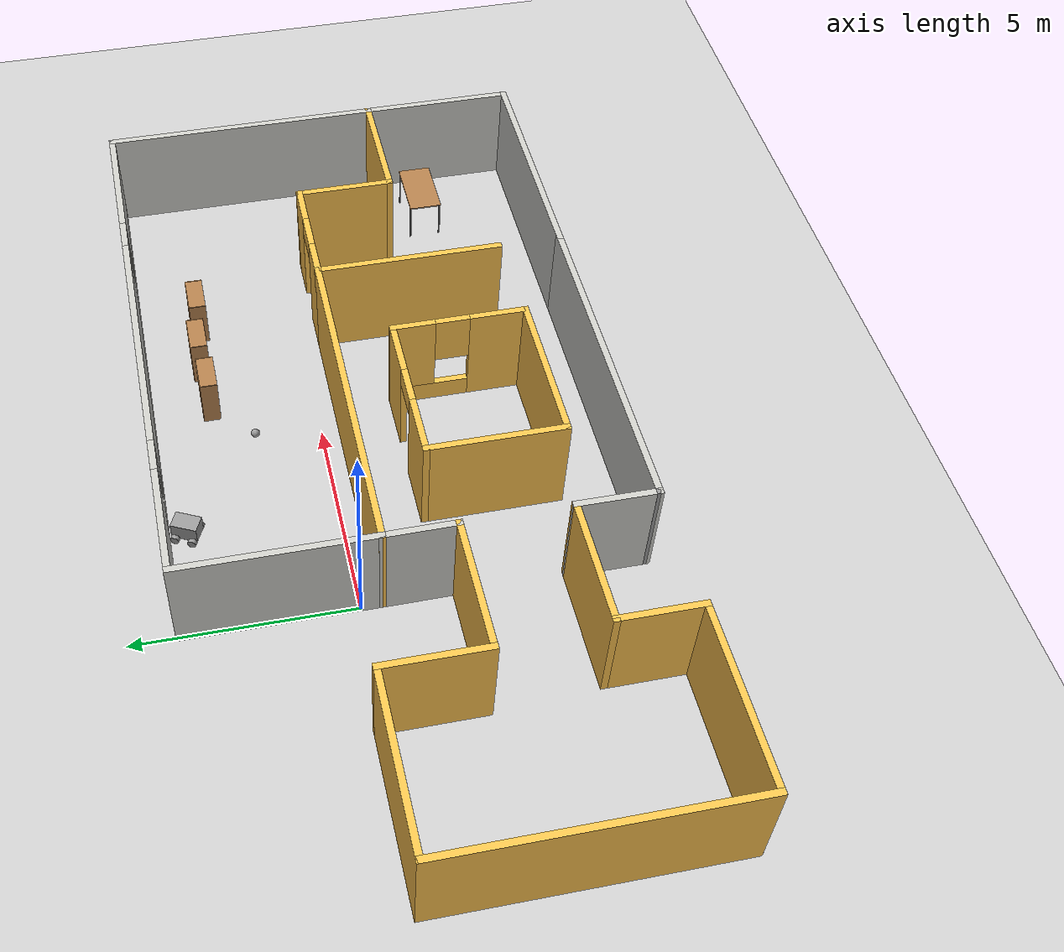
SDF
<sdf version="1.6">
 <world name="default">
  <plugin name="welcome_message" filename="libwelcome_message.so"/>
  <light name="sun" type="directional">
   <pose>0 0 10 0 -0 0</pose>
   <diffuse>0.8 0.8 0.8 1</diffuse>
   <specular>0.2 0.2 0.2 1</specular>
   <attenuation>
    <range>1000</range>
    <constant>0.9</constant>
    <linear>0.01</linear>
    <quadratic>0.001</quadratic>
   </attenuation>
   <direction>-0.5 0.1 -0.9</direction>
  </light>
  <model name="ground_plane">
   <static>1</static>
   <link name="link">
    <collision name="collision">
     <geometry><plane><normal>0 0 1</normal><size>100 100</size></plane></geometry>
     <surface>
      <contact><collide_bitmask>65535</collide_bitmask></contact>
      <friction><ode><mu>100</mu><mu2>50</mu2></ode></friction>
     </surface>
    </collision>
    <visual name="visual">
     <cast_shadows>0</cast_shadows>
     <geometry><plane><normal>0 0 1</normal><size>100 100</size></plane></geometry>
     <material>
      <script><uri>file://media/materials/scripts/gazebo.material</uri><name>Gazebo/Grey</name></script>
     </material>
    </visual>
   </link>
  </model>
  <gravity>0 0 -9.8</gravity>
  <magnetic_field>6e-06 2.3e-05 -4.2e-05</magnetic_field>
  <atmosphere type="adiabatic"/>
  <physics name="default_physics" default="0" type="ode">
   <max_step_size>0.001</max_step_size>
   <real_time_factor>1</real_time_factor>
   <real_time_update_rate>1000</real_time_update_rate>
  </physics>
  <scene><ambient>0.4 0.4 0.4 1</ambient><background>0.7 0.7 0.7 1</background><shadows>1</shadows></scene>
  <spherical_coordinates>
   <surface_model>EARTH_WGS84</surface_model>
   <latitude_deg>0</latitude_deg>
   <longitude_deg>0</longitude_deg>
   <elevation>0</elevation>
   <heading_deg>0</heading_deg>
  </spherical_coordinates>
  <model name="building">
   <pose>3.27409 -1.24254 0 0 -0 0</pose>
   <link name="Wall_1">
    <collision name="Wall_1_Collision">
     <geometry><box><size>0.15 0.15 2.5</size></box></geometry>
     <pose>0 0 1.25 0 -0 0</pose>
    </collision>
    <visual name="Wall_1_Visual">
     <pose>0 0 1.25 0 -0 0</pose>
     <geometry><box><size>0.15 0.15 2.5</size></box></geometry>
     <material>
      <script><uri>file://media/materials/scripts/gazebo.material</uri><name>Gazebo/Grey</name></script>
      <ambient>1 1 1 1</ambient>
     </material>
     <meta><layer>0</layer></meta>
    </visual>
    <pose>-3.253 -5.0694 0 0 -0 0</pose>
   </link>
   <link name="Wall_10">
    <collision name="Wall_10_Collision">
     <geometry><box><size>3 0.15 2.5</size></box></geometry>
     <pose>0 0 1.25 0 -0 0</pose>
    </collision>
    <visual name="Wall_10_Visual">
     <pose>0 0 1.25 0 -0 0</pose>
     <geometry><box><size>3 0.15 2.5</size></box></geometry>
     <material>
      <script><uri>file://media/materials/scripts/gazebo.material</uri><name>Gazebo/Grey</name></script>
      <ambient>1 0.764706 0.305882 1</ambient>
     </material>
     <meta><layer>0</layer></meta>
    </visual>
    <pose>8.772 -1.4694 0 0 -0 3.14159</pose>
   </link>
   <link name="Wall_11">
    <collision name="Wall_11_Collision">
     <geometry><box><size>2.4 0.15 2.5</size></box></geometry>
     <pose>0 0 1.25 0 -0 0</pose>
    </collision>
    <visual name="Wall_11_Visual">
     <pose>0 0 1.25 0 -0 0</pose>
     <geometry><box><size>2.4 0.15 2.5</size></box></geometry>
     <material>
      <script><uri>file://media/materials/scripts/gazebo.material</uri><name>Gazebo/Grey</name></script>
      <ambient>1 0.764706 0.305882 1</ambient>
     </material>
     <meta><layer>0</layer></meta>
    </visual>
    <pose>7.347 -0.344396 0 0 -0 1.5708</pose>
   </link>
   <link name="Wall_14">
    <pose>5.972 0.780604 0 0 -0 0</pose>
    <visual name="Wall_14_Visual_0">
     <pose>-0.96253 0 1.25 0 -0 0</pose>
     <geometry><box><size>0.974941 0.15 2.5</size></box></geometry>
     <material>
      <script><uri>file://media/materials/scripts/gazebo.material</uri><name>Gazebo/Grey</name></script>
      <ambient>1 0.764706 0.305882 1</ambient>
     </material>
     <meta><layer>0</layer></meta>
    </visual>
    <collision name="Wall_14_Collision_0">
     <geometry><box><size>0.974941 0.15 2.5</size></box></geometry>
     <pose>-0.96253 0 1.25 0 -0 0</pose>
    </collision>
    <visual name="Wall_14_Visual_1">
     <pose>0.93747 0 1.25 0 -0 0</pose>
     <geometry><box><size>1.02506 0.15 2.5</size></box></geometry>
     <material>
      <script><uri>file://media/materials/scripts/gazebo.material</uri><name>Gazebo/Grey</name></script>
      <ambient>1 0.764706 0.305882 1</ambient>
     </material>
     <meta><layer>0</layer></meta>
    </visual>
    <collision name="Wall_14_Collision_1">
     <geometry><box><size>1.02506 0.15 2.5</size></box></geometry>
     <pose>0.93747 0 1.25 0 -0 0</pose>
    </collision>
    <visual name="Wall_14_Visual_2">
     <pose>-0.025059 0 2.25 0 -0 0</pose>
     <geometry><box><size>0.9 0.15 0.5</size></box></geometry>
     <material>
      <script><uri>file://media/materials/scripts/gazebo.material</uri><name>Gazebo/Grey</name></script>
      <ambient>1 0.764706 0.305882 1</ambient>
     </material>
     <meta><layer>0</layer></meta>
    </visual>
    <collision name="Wall_14_Collision_2">
     <geometry><box><size>0.9 0.15 0.5</size></box></geometry>
     <pose>-0.025059 0 2.25 0 -0 0</pose>
    </collision>
   </link>
   <link name="Wall_17">
    <collision name="Wall_17_Collision">
     <geometry><box><size>3 0.15 2.5</size></box></geometry>
     <pose>0 0 1.25 0 -0 0</pose>
    </collision>
    <visual name="Wall_17_Visual">
     <pose>0 0 1.25 0 -0 0</pose>
     <geometry><box><size>3 0.15 2.5</size></box></geometry>
     <material>
      <script><uri>file://media/materials/scripts/gazebo.material</uri><name>Gazebo/Grey</name></script>
      <ambient>1 0.764706 0.305882 1</ambient>
     </material>
     <meta><layer>0</layer></meta>
    </visual>
    <pose>-4.67154 -0.826749 0 0 -0 3.14159</pose>
   </link>
   <link name="Wall_19">
    <collision name="Wall_19_Collision">
     <geometry><box><size>3 0.15 2.5</size></box></geometry>
     <pose>0 0 1.25 0 -0 0</pose>
    </collision>
    <visual name="Wall_19_Visual">
     <pose>0 0 1.25 0 -0 0</pose>
     <geometry><box><size>3 0.15 2.5</size></box></geometry>
     <material>
      <script><uri>file://media/materials/scripts/gazebo.material</uri><name>Gazebo/Grey</name></script>
      <ambient>1 0.764706 0.305882 1</ambient>
     </material>
     <meta><layer>0</layer></meta>
    </visual>
    <pose>-4.67154 -3.2806 0 0 -0 3.14159</pose>
   </link>
   <link name="Wall_20">
    <collision name="Wall_20_Collision">
     <geometry><box><size>2 0.15 2.5</size></box></geometry>
     <pose>0 0 1.25 0 -0 0</pose>
    </collision>
    <visual name="Wall_20_Visual">
     <pose>0 0 1.25 0 -0 0</pose>
     <geometry><box><size>2 0.15 2.5</size></box></geometry>
     <material>
      <script><uri>file://media/materials/scripts/gazebo.material</uri><name>Gazebo/Grey</name></script>
      <ambient>1 0.764706 0.305882 1</ambient>
     </material>
     <meta><layer>0</layer></meta>
    </visual>
    <pose>-6.09654 -4.2056 0 0 0 -1.5708</pose>
   </link>
   <link name="Wall_21">
    <collision name="Wall_21_Collision">
     <geometry><box><size>4.25 0.15 2.5</size></box></geometry>
     <pose>0 0 1.25 0 -0 0</pose>
    </collision>
    <visual name="Wall_21_Visual">
     <pose>0 0 1.25 0 -0 0</pose>
     <geometry><box><size>4.25 0.15 2.5</size></box></geometry>
     <material>
      <script><uri>file://media/materials/scripts/gazebo.material</uri><name>Gazebo/Grey</name></script>
      <ambient>1 0.764706 0.305882 1</ambient>
     </material>
     <meta><layer>0</layer></meta>
    </visual>
    <pose>-8.14654 -5.13061 0 0 -0 3.14159</pose>
   </link>
   <link name="Wall_22">
    <collision name="Wall_22_Collision">
     <geometry><box><size>6.75 0.15 2.5</size></box></geometry>
     <pose>0 0 1.25 0 -0 0</pose>
    </collision>
    <visual name="Wall_22_Visual">
     <pose>0 0 1.25 0 -0 0</pose>
     <geometry><box><size>6.75 0.15 2.5</size></box></geometry>
     <material>
      <script><uri>file://media/materials/scripts/gazebo.material</uri><name>Gazebo/Grey</name></script>
      <ambient>1 0.764706 0.305882 1</ambient>
     </material>
     <meta><layer>0</layer></meta>
    </visual>
    <pose>-10.1968 -1.8305 0 0 -0 1.57087</pose>
   </link>
   <link name="Wall_23">
    <collision name="Wall_23_Collision">
     <geometry><box><size>4.1 0.15 2.5</size></box></geometry>
     <pose>0 0 1.25 0 -0 0</pose>
    </collision>
    <visual name="Wall_23_Visual">
     <pose>0 0 1.25 0 -0 0</pose>
     <geometry><box><size>4.1 0.15 2.5</size></box></geometry>
     <material>
      <script><uri>file://media/materials/scripts/gazebo.material</uri><name>Gazebo/Grey</name></script>
      <ambient>1 0.764706 0.305882 1</ambient>
     </material>
     <meta><layer>0</layer></meta>
    </visual>
    <pose>-8.222 1.4696 0 0 -0 0</pose>
   </link>
   <link name="Wall_25">
    <collision name="Wall_25_Collision">
     <geometry><box><size>2.45 0.15 2.5</size></box></geometry>
     <pose>0 0 1.25 0 -0 0</pose>
    </collision>
    <visual name="Wall_25_Visual">
     <pose>0 0 1.25 0 -0 0</pose>
     <geometry><box><size>2.45 0.15 2.5</size></box></geometry>
     <material>
      <script><uri>file://media/materials/scripts/gazebo.material</uri><name>Gazebo/Grey</name></script>
      <ambient>1 0.764706 0.305882 1</ambient>
     </material>
     <meta><layer>0</layer></meta>
    </visual>
    <pose>-6.247 0.319604 0 0 0 -1.5708</pose>
   </link>
   <link name="Wall_28">
    <collision name="Wall_28_Collision">
     <geometry><box><size>3.25 0.15 2.5</size></box></geometry>
     <pose>0 0 1.25 0 -0 0</pose>
    </collision>
    <visual name="Wall_28_Visual">
     <pose>0 0 1.25 0 -0 0</pose>
     <geometry><box><size>3.25 0.15 2.5</size></box></geometry>
     <material>
      <script><uri>file://media/materials/scripts/gazebo.material</uri><name>Gazebo/Grey</name></script>
      <ambient>1 0.764706 0.305882 1</ambient>
     </material>
     <meta><layer>0</layer></meta>
    </visual>
    <pose>-1.19495 -2.11527 0 0 0 -1.5708</pose>
   </link>
   <link name="Wall_29">
    <collision name="Wall_29_Collision">
     <geometry><box><size>3.75 0.15 2.5</size></box></geometry>
     <pose>0 0 1.25 0 -0 0</pose>
    </collision>
    <visual name="Wall_29_Visual">
     <pose>0 0 1.25 0 -0 0</pose>
     <geometry><box><size>3.75 0.15 2.5</size></box></geometry>
     <material>
      <script><uri>file://media/materials/scripts/gazebo.material</uri><name>Gazebo/Grey</name></script>
      <ambient>1 0.764706 0.305882 1</ambient>
     </material>
     <meta><layer>0</layer></meta>
    </visual>
    <pose>0.605046 -3.66527 0 0 -0 0</pose>
   </link>
   <link name="Wall_30">
    <pose>2.40505 -2.11527 0 0 -0 1.5708</pose>
    <visual name="Wall_30_Visual_0">
     <pose>-0.931418 0 1.25 0 -0 0</pose>
     <geometry><box><size>1.38716 0.15 2.5</size></box></geometry>
     <material>
      <script><uri>file://media/materials/scripts/gazebo.material</uri><name>Gazebo/Grey</name></script>
      <ambient>1 0.764706 0.305882 1</ambient>
     </material>
     <meta><layer>0</layer></meta>
    </visual>
    <collision name="Wall_30_Collision_0">
     <geometry><box><size>1.38716 0.15 2.5</size></box></geometry>
     <pose>-0.931418 0 1.25 0 -0 0</pose>
    </collision>
    <visual name="Wall_30_Visual_1">
     <pose>0.693582 0 0.25 0 -0 0</pose>
     <geometry><box><size>1.86284 0.15 0.5</size></box></geometry>
     <material>
      <script><uri>file://media/materials/scripts/gazebo.material</uri><name>Gazebo/Grey</name></script>
      <ambient>1 0.764706 0.305882 1</ambient>
     </material>
     <meta><layer>0</layer></meta>
    </visual>
    <collision name="Wall_30_Collision_1">
     <geometry><box><size>1.86284 0.15 0.5</size></box></geometry>
     <pose>0.693582 0 0.25 0 -0 0</pose>
    </collision>
    <visual name="Wall_30_Visual_2">
     <pose>1.09358 0 1.5 0 -0 0</pose>
     <geometry><box><size>1.06284 0.15 2</size></box></geometry>
     <material>
      <script><uri>file://media/materials/scripts/gazebo.material</uri><name>Gazebo/Grey</name></script>
      <ambient>1 0.764706 0.305882 1</ambient>
     </material>
     <meta><layer>0</layer></meta>
    </visual>
    <collision name="Wall_30_Collision_2">
     <geometry><box><size>1.06284 0.15 2</size></box></geometry>
     <pose>1.09358 0 1.5 0 -0 0</pose>
    </collision>
    <visual name="Wall_30_Visual_3">
     <pose>0.162163 0 1.9 0 -0 0</pose>
     <geometry><box><size>0.8 0.15 1.2</size></box></geometry>
     <material>
      <script><uri>file://media/materials/scripts/gazebo.material</uri><name>Gazebo/Grey</name></script>
      <ambient>1 0.764706 0.305882 1</ambient>
     </material>
     <meta><layer>0</layer></meta>
    </visual>
    <collision name="Wall_30_Collision_3">
     <geometry><box><size>0.8 0.15 1.2</size></box></geometry>
     <pose>0.162163 0 1.9 0 -0 0</pose>
    </collision>
   </link>
   <link name="Wall_31">
    <pose>0.605046 -0.565272 0 0 -0 3.14159</pose>
    <visual name="Wall_31_Visual_0">
     <pose>-1.18772 0 1.25 0 -0 0</pose>
     <geometry><box><size>1.37455 0.15 2.5</size></box></geometry>
     <material>
      <script><uri>file://media/materials/scripts/gazebo.material</uri><name>Gazebo/Grey</name></script>
      <ambient>1 0.764706 0.305882 1</ambient>
     </material>
     <meta><layer>0</layer></meta>
    </visual>
    <collision name="Wall_31_Collision_0">
     <geometry><box><size>1.37455 0.15 2.5</size></box></geometry>
     <pose>-1.18772 0 1.25 0 -0 0</pose>
    </collision>
    <visual name="Wall_31_Visual_1">
     <pose>1.13728 0 1.25 0 -0 0</pose>
     <geometry><box><size>1.47545 0.15 2.5</size></box></geometry>
     <material>
      <script><uri>file://media/materials/scripts/gazebo.material</uri><name>Gazebo/Grey</name></script>
      <ambient>1 0.764706 0.305882 1</ambient>
     </material>
     <meta><layer>0</layer></meta>
    </visual>
    <collision name="Wall_31_Collision_1">
     <geometry><box><size>1.47545 0.15 2.5</size></box></geometry>
     <pose>1.13728 0 1.25 0 -0 0</pose>
    </collision>
    <visual name="Wall_31_Visual_2">
     <pose>-0.050449 0 2.25 0 -0 0</pose>
     <geometry><box><size>0.9 0.15 0.5</size></box></geometry>
     <material>
      <script><uri>file://media/materials/scripts/gazebo.material</uri><name>Gazebo/Grey</name></script>
      <ambient>1 0.764706 0.305882 1</ambient>
     </material>
     <meta><layer>0</layer></meta>
    </visual>
    <collision name="Wall_31_Collision_2">
     <geometry><box><size>0.9 0.15 0.5</size></box></geometry>
     <pose>-0.050449 0 2.25 0 -0 0</pose>
    </collision>
   </link>
   <link name="Wall_33">
    <collision name="Wall_33_Collision">
     <geometry><box><size>4.5 0.15 2.5</size></box></geometry>
     <pose>0 0 1.25 0 -0 0</pose>
    </collision>
    <visual name="Wall_33_Visual">
     <pose>0 0 1.25 0 -0 0</pose>
     <geometry><box><size>4.5 0.15 2.5</size></box></geometry>
     <material>
      <script><uri>file://media/materials/scripts/gazebo.material</uri><name>Gazebo/CeilingTiled</name></script>
      <ambient>1 1 1 1</ambient>
     </material>
     <meta><layer>0</layer></meta>
    </visual>
    <pose>-3.253 2.9556 0 0 -0 1.5708</pose>
   </link>
   <link name="Wall_34">
    <pose>3.472 5.1306 0 0 -0 0</pose>
    <visual name="Wall_34_Visual_0">
     <pose>-5.46145 0 1.25 0 -0 0</pose>
     <geometry><box><size>2.6771 0.15 2.5</size></box></geometry>
     <material>
      <script><uri>file://media/materials/scripts/gazebo.material</uri><name>Gazebo/CeilingTiled</name></script>
      <ambient>1 1 1 1</ambient>
     </material>
     <meta><layer>0</layer></meta>
    </visual>
    <collision name="Wall_34_Collision_0">
     <geometry><box><size>2.6771 0.15 2.5</size></box></geometry>
     <pose>-5.46145 0 1.25 0 -0 0</pose>
    </collision>
    <visual name="Wall_34_Visual_1">
     <pose>1.33855 0 0.25 0 -0 0</pose>
     <geometry><box><size>10.9229 0.15 0.5</size></box></geometry>
     <material>
      <script><uri>file://media/materials/scripts/gazebo.material</uri><name>Gazebo/CeilingTiled</name></script>
      <ambient>1 1 1 1</ambient>
     </material>
     <meta><layer>0</layer></meta>
    </visual>
    <collision name="Wall_34_Collision_1">
     <geometry><box><size>10.9229 0.15 0.5</size></box></geometry>
     <pose>1.33855 0 0.25 0 -0 0</pose>
    </collision>
    <visual name="Wall_34_Visual_2">
     <pose>-0.25158 0 1.5 0 -0 0</pose>
     <geometry><box><size>6.14265 0.15 2</size></box></geometry>
     <material>
      <script><uri>file://media/materials/scripts/gazebo.material</uri><name>Gazebo/CeilingTiled</name></script>
      <ambient>1 1 1 1</ambient>
     </material>
     <meta><layer>0</layer></meta>
    </visual>
    <collision name="Wall_34_Collision_2">
     <geometry><box><size>6.14265 0.15 2</size></box></geometry>
     <pose>-0.25158 0 1.5 0 -0 0</pose>
    </collision>
    <visual name="Wall_34_Visual_3">
     <pose>5.20987 0 1.5 0 -0 0</pose>
     <geometry><box><size>3.18025 0.15 2</size></box></geometry>
     <material>
      <script><uri>file://media/materials/scripts/gazebo.material</uri><name>Gazebo/CeilingTiled</name></script>
      <ambient>1 1 1 1</ambient>
     </material>
     <meta><layer>0</layer></meta>
    </visual>
    <collision name="Wall_34_Collision_3">
     <geometry><box><size>3.18025 0.15 2</size></box></geometry>
     <pose>5.20987 0 1.5 0 -0 0</pose>
    </collision>
    <visual name="Wall_34_Visual_4">
     <pose>-3.7229 0 1.9 0 -0 0</pose>
     <geometry><box><size>0.8 0.15 1.2</size></box></geometry>
     <material>
      <script><uri>file://media/materials/scripts/gazebo.material</uri><name>Gazebo/CeilingTiled</name></script>
      <ambient>1 1 1 1</ambient>
     </material>
     <meta><layer>0</layer></meta>
    </visual>
    <collision name="Wall_34_Collision_4">
     <geometry><box><size>0.8 0.15 1.2</size></box></geometry>
     <pose>-3.7229 0 1.9 0 -0 0</pose>
    </collision>
    <visual name="Wall_34_Visual_5">
     <pose>3.21975 0 1.9 0 -0 0</pose>
     <geometry><box><size>0.8 0.15 1.2</size></box></geometry>
     <material>
      <script><uri>file://media/materials/scripts/gazebo.material</uri><name>Gazebo/CeilingTiled</name></script>
      <ambient>1 1 1 1</ambient>
     </material>
     <meta><layer>0</layer></meta>
    </visual>
    <collision name="Wall_34_Collision_5">
     <geometry><box><size>0.8 0.15 1.2</size></box></geometry>
     <pose>3.21975 0 1.9 0 -0 0</pose>
    </collision>
   </link>
   <link name="Wall_37">
    <collision name="Wall_37_Collision">
     <geometry><box><size>6.75 0.15 2.5</size></box></geometry>
     <pose>0 0 1.25 0 -0 0</pose>
    </collision>
    <visual name="Wall_37_Visual">
     <pose>0 0 1.25 0 -0 0</pose>
     <geometry><box><size>6.75 0.15 2.5</size></box></geometry>
     <material>
      <script><uri>file://media/materials/scripts/gazebo.material</uri><name>Gazebo/CeilingTiled</name></script>
      <ambient>1 1 1 1</ambient>
     </material>
     <meta><layer>0</layer></meta>
    </visual>
    <pose>10.197 1.8306 0 0 0 -1.5708</pose>
   </link>
   <link name="Wall_4">
    <collision name="Wall_4_Collision">
     <geometry><box><size>8 0.15 2.5</size></box></geometry>
     <pose>0 0 1.25 0 -0 0</pose>
    </collision>
    <visual name="Wall_4_Visual">
     <pose>0 0 1.25 0 -0 0</pose>
     <geometry><box><size>8 0.15 2.5</size></box></geometry>
     <material>
      <script><uri>file://media/materials/scripts/gazebo.material</uri><name>Gazebo/Grey</name></script>
      <ambient>1 0.764706 0.305882 1</ambient>
     </material>
     <meta><layer>0</layer></meta>
    </visual>
    <pose>0.672003 0.780604 0 0 -0 0</pose>
   </link>
   <link name="Wall_40">
    <collision name="Wall_40_Collision">
     <geometry><box><size>1.75737 0.15 2.5</size></box></geometry>
     <pose>0 0 1.25 0 -0 0</pose>
    </collision>
    <visual name="Wall_40_Visual">
     <pose>0 0 1.25 0 -0 0</pose>
     <geometry><box><size>1.75737 0.15 2.5</size></box></geometry>
     <material>
      <script><uri>file://media/materials/scripts/gazebo.material</uri><name>Gazebo/CeilingTiled</name></script>
      <ambient>1 1 1 1</ambient>
     </material>
     <meta><layer>0</layer></meta>
    </visual>
    <pose>-3.24977 -0.023072 0 0 -0 1.57481</pose>
   </link>
   <link name="Wall_42">
    <collision name="Wall_42_Collision">
     <geometry><box><size>1.9388 0.15 2.5</size></box></geometry>
     <pose>0 0 1.25 0 -0 0</pose>
    </collision>
    <visual name="Wall_42_Visual">
     <pose>0 0 1.25 0 -0 0</pose>
     <geometry><box><size>1.9388 0.15 2.5</size></box></geometry>
     <material>
      <script><uri>file://media/materials/scripts/gazebo.material</uri><name>Gazebo/CeilingTiled</name></script>
      <ambient>1 1 1 1</ambient>
     </material>
     <meta><layer>0</layer></meta>
    </visual>
    <pose>-3.24977 -4.175 0 0 -0 1.56719</pose>
   </link>
   <link name="Wall_44">
    <collision name="Wall_44_Collision">
     <geometry><box><size>4.5 0.15 2.5</size></box></geometry>
     <pose>0 0 1.25 0 -0 0</pose>
    </collision>
    <visual name="Wall_44_Visual">
     <pose>0 0 1.25 0 -0 0</pose>
     <geometry><box><size>4.5 0.15 2.5</size></box></geometry>
     <material>
      <script><uri>file://media/materials/scripts/gazebo.material</uri><name>Gazebo/Grey</name></script>
      <ambient>1 0.764706 0.305882 1</ambient>
     </material>
     <meta><layer>0</layer></meta>
    </visual>
    <pose>4.597 -1.3944 0 0 0 -1.5708</pose>
   </link>
   <link name="Wall_7">
    <collision name="Wall_7_Collision">
     <geometry><box><size>8 0.15 2.5</size></box></geometry>
     <pose>0 0 1.25 0 -0 0</pose>
    </collision>
    <visual name="Wall_7_Visual">
     <pose>0 0 1.25 0 -0 0</pose>
     <geometry><box><size>8 0.15 2.5</size></box></geometry>
     <material>
      <script><uri>file://media/materials/scripts/gazebo.material</uri><name>Gazebo/CeilingTiled</name></script>
      <ambient>1 1 1 1</ambient>
     </material>
     <meta><layer>0</layer></meta>
    </visual>
    <pose>0.672003 -5.0694 0 0 -0 0</pose>
   </link>
   <link name="Wall_8">
    <collision name="Wall_8_Collision">
     <geometry><box><size>5.75 0.15 2.5</size></box></geometry>
     <pose>0 0 1.25 0 -0 0</pose>
    </collision>
    <visual name="Wall_8_Visual">
     <pose>0 0 1.25 0 -0 0</pose>
     <geometry><box><size>5.75 0.15 2.5</size></box></geometry>
     <material>
      <script><uri>file://media/materials/scripts/gazebo.material</uri><name>Gazebo/CeilingTiled</name></script>
      <ambient>1 1 1 1</ambient>
     </material>
     <meta><layer>0</layer></meta>
    </visual>
    <pose>7.397 -5.0694 0 0 -0 0</pose>
   </link>
   <link name="Wall_9">
    <collision name="Wall_9_Collision">
     <geometry><box><size>3.75 0.15 2.5</size></box></geometry>
     <pose>0 0 1.25 0 -0 0</pose>
    </collision>
    <visual name="Wall_9_Visual">
     <pose>0 0 1.25 0 -0 0</pose>
     <geometry><box><size>3.75 0.15 2.5</size></box></geometry>
     <material>
      <script><uri>file://media/materials/scripts/gazebo.material</uri><name>Gazebo/CeilingTiled</name></script>
      <ambient>1 1 1 1</ambient>
     </material>
     <meta><layer>0</layer></meta>
    </visual>
    <pose>10.197 -3.2694 0 0 -0 1.5708</pose>
   </link>
   <static>1</static>
  </model>
  <model name="wayhicle">
   <link name="link_0">
    <pose>0 0 0.16 0 -0 0</pose>
    <inertial>
     <mass>1</mass>
     <inertia>
      <ixx>0.166667</ixx>
      <ixy>0</ixy>
      <ixz>0</ixz>
      <iyy>0.166667</iyy>
      <iyz>0</iyz>
      <izz>0.166667</izz>
     </inertia>
    </inertial>
    <visual name="visual">
     <geometry><box><size>0.4 0.6 0.4</size></box></geometry>
     <material>
      <lighting>1</lighting>
      <script><uri>file://media/materials/scripts/gazebo.material</uri><name>Gazebo/Grey</name></script>
      <shader type="pixel"><normal_map>__default__</normal_map></shader>
      <ambient>0.3 0.3 0.3 1</ambient>
      <diffuse>0.7 0.7 0.7 1</diffuse>
      <specular>0.01 0.01 0.01 1</specular>
      <emissive>0 0 0 1</emissive>
     </material>
    </visual>
    <collision name="collision">
     <geometry><box><size>0.4 0.6 0.4</size></box></geometry>
     <surface>
      <friction>
       <ode><mu>1</mu><mu2>1</mu2><fdir1>0 0 0</fdir1><slip1>0</slip1><slip2>0</slip2></ode>
       <torsional>
        <coefficient>1</coefficient>
        <patch_radius>0</patch_radius>
        <surface_radius>0</surface_radius>
        <use_patch_radius>1</use_patch_radius>
        <ode><slip>0</slip></ode>
       </torsional>
      </friction>
      <bounce><restitution_coefficient>0</restitution_coefficient><threshold>1e+06</threshold></bounce>
      <contact>
       <collide_without_contact>0</collide_without_contact>
       <collide_without_contact_bitmask>1</collide_without_contact_bitmask>
       <collide_bitmask>1</collide_bitmask>
       <ode>
        <soft_cfm>0</soft_cfm>
        <soft_erp>0.2</soft_erp>
        <kp>1e+13</kp>
        <kd>1</kd>
        <max_vel>0.01</max_vel>
        <min_depth>0</min_depth>
       </ode>
       <bullet>
        <split_impulse>1</split_impulse>
        <split_impulse_penetration_threshold>-0.01</split_impulse_penetration_threshold>
        <soft_cfm>0</soft_cfm>
        <soft_erp>0.2</soft_erp>
        <kp>1e+13</kp>
        <kd>1</kd>
       </bullet>
      </contact>
     </surface>
    </collision>
   </link>
   <link name="link_1">
    <pose>-0.25 -0.2 -0.04 1.5708 -0 1.5708</pose>
    <inertial>
     <mass>0.3</mass>
     <inertia><ixx>0.145833</ixx><ixy>0</ixy><ixz>0</ixz><iyy>0.145833</iyy><iyz>0</iyz><izz>0.125</izz></inertia>
    </inertial>
    <visual name="visual">
     <geometry><cylinder><radius>0.1</radius><length>0.1</length></cylinder></geometry>
     <material>
      <lighting>1</lighting>
      <script><uri>file://media/materials/scripts/gazebo.material</uri><name>Gazebo/Grey</name></script>
      <shader type="pixel"><normal_map>__default__</normal_map></shader>
      <ambient>0.3 0.3 0.3 1</ambient>
      <diffuse>0.7 0.7 0.7 1</diffuse>
      <specular>0.01 0.01 0.01 1</specular>
      <emissive>0 0 0 1</emissive>
     </material>
    </visual>
    <collision name="collision">
     <geometry><cylinder><radius>0.1</radius><length>0.1</length></cylinder></geometry>
     <surface>
      <friction>
       <ode><mu>1</mu><mu2>1</mu2><fdir1>0 0 0</fdir1><slip1>0</slip1><slip2>0</slip2></ode>
       <torsional>
        <coefficient>1</coefficient>
        <patch_radius>0</patch_radius>
        <surface_radius>0</surface_radius>
        <use_patch_radius>1</use_patch_radius>
        <ode><slip>0</slip></ode>
       </torsional>
      </friction>
      <bounce><restitution_coefficient>0</restitution_coefficient><threshold>1e+06</threshold></bounce>
      <contact>
       <collide_without_contact>0</collide_without_contact>
       <collide_without_contact_bitmask>1</collide_without_contact_bitmask>
       <collide_bitmask>1</collide_bitmask>
       <ode>
        <soft_cfm>0</soft_cfm>
        <soft_erp>0.2</soft_erp>
        <kp>1e+13</kp>
        <kd>1</kd>
        <max_vel>0.01</max_vel>
        <min_depth>0</min_depth>
       </ode>
       <bullet>
        <split_impulse>1</split_impulse>
        <split_impulse_penetration_threshold>-0.01</split_impulse_penetration_threshold>
        <soft_cfm>0</soft_cfm>
        <soft_erp>0.2</soft_erp>
        <kp>1e+13</kp>
        <kd>1</kd>
       </bullet>
      </contact>
     </surface>
    </collision>
   </link>
   <link name="link_1_clone">
    <pose>-0.25 0.2 -0.04 1.5708 -0 1.5708</pose>
    <inertial>
     <mass>0.3</mass>
     <inertia><ixx>0.145833</ixx><ixy>0</ixy><ixz>0</ixz><iyy>0.145833</iyy><iyz>0</iyz><izz>0.125</izz></inertia>
    </inertial>
    <visual name="visual">
     <geometry><cylinder><radius>0.1</radius><length>0.1</length></cylinder></geometry>
     <material>
      <lighting>1</lighting>
      <script><uri>file://media/materials/scripts/gazebo.material</uri><name>Gazebo/Grey</name></script>
      <shader type="pixel"><normal_map>__default__</normal_map></shader>
      <ambient>0.3 0.3 0.3 1</ambient>
      <diffuse>0.7 0.7 0.7 1</diffuse>
      <specular>0.01 0.01 0.01 1</specular>
      <emissive>0 0 0 1</emissive>
     </material>
    </visual>
    <collision name="collision">
     <geometry><cylinder><radius>0.1</radius><length>0.1</length></cylinder></geometry>
     <surface>
      <friction>
       <ode><mu>1</mu><mu2>1</mu2><fdir1>0 0 0</fdir1><slip1>0</slip1><slip2>0</slip2></ode>
       <torsional>
        <coefficient>1</coefficient>
        <patch_radius>0</patch_radius>
        <surface_radius>0</surface_radius>
        <use_patch_radius>1</use_patch_radius>
        <ode><slip>0</slip></ode>
       </torsional>
      </friction>
      <bounce><restitution_coefficient>0</restitution_coefficient><threshold>1e+06</threshold></bounce>
      <contact>
       <collide_without_contact>0</collide_without_contact>
       <collide_without_contact_bitmask>1</collide_without_contact_bitmask>
       <collide_bitmask>1</collide_bitmask>
       <ode>
        <soft_cfm>0</soft_cfm>
        <soft_erp>0.2</soft_erp>
        <kp>1e+13</kp>
        <kd>1</kd>
        <max_vel>0.01</max_vel>
        <min_depth>0</min_depth>
       </ode>
       <bullet>
        <split_impulse>1</split_impulse>
        <split_impulse_penetration_threshold>-0.01</split_impulse_penetration_threshold>
        <soft_cfm>0</soft_cfm>
        <soft_erp>0.2</soft_erp>
        <kp>1e+13</kp>
        <kd>1</kd>
       </bullet>
      </contact>
     </surface>
    </collision>
   </link>
   <link name="link_1_clone_0">
    <pose>0.25 -0.2 -0.04 1.5708 -0 1.5708</pose>
    <inertial>
     <mass>0.3</mass>
     <inertia><ixx>0.145833</ixx><ixy>0</ixy><ixz>0</ixz><iyy>0.145833</iyy><iyz>0</iyz><izz>0.125</izz></inertia>
    </inertial>
    <visual name="visual">
     <geometry><cylinder><radius>0.1</radius><length>0.1</length></cylinder></geometry>
     <material>
      <lighting>1</lighting>
      <script><uri>file://media/materials/scripts/gazebo.material</uri><name>Gazebo/Grey</name></script>
      <shader type="pixel"><normal_map>__default__</normal_map></shader>
      <ambient>0.3 0.3 0.3 1</ambient>
      <diffuse>0.7 0.7 0.7 1</diffuse>
      <specular>0.01 0.01 0.01 1</specular>
      <emissive>0 0 0 1</emissive>
     </material>
    </visual>
    <collision name="collision">
     <geometry><cylinder><radius>0.1</radius><length>0.1</length></cylinder></geometry>
     <surface>
      <friction>
       <ode><mu>1</mu><mu2>1</mu2><fdir1>0 0 0</fdir1><slip1>0</slip1><slip2>0</slip2></ode>
       <torsional>
        <coefficient>1</coefficient>
        <patch_radius>0</patch_radius>
        <surface_radius>0</surface_radius>
        <use_patch_radius>1</use_patch_radius>
        <ode><slip>0</slip></ode>
       </torsional>
      </friction>
      <bounce><restitution_coefficient>0</restitution_coefficient><threshold>1e+06</threshold></bounce>
      <contact>
       <collide_without_contact>0</collide_without_contact>
       <collide_without_contact_bitmask>1</collide_without_contact_bitmask>
       <collide_bitmask>1</collide_bitmask>
       <ode>
        <soft_cfm>0</soft_cfm>
        <soft_erp>0.2</soft_erp>
        <kp>1e+13</kp>
        <kd>1</kd>
        <max_vel>0.01</max_vel>
        <min_depth>0</min_depth>
       </ode>
       <bullet>
        <split_impulse>1</split_impulse>
        <split_impulse_penetration_threshold>-0.01</split_impulse_penetration_threshold>
        <soft_cfm>0</soft_cfm>
        <soft_erp>0.2</soft_erp>
        <kp>1e+13</kp>
        <kd>1</kd>
       </bullet>
      </contact>
     </surface>
    </collision>
   </link>
   <link name="link_1_clone_1">
    <pose>0.25 0.2 -0.04 1.5708 -0 1.5708</pose>
    <inertial>
     <mass>0.3</mass>
     <inertia><ixx>0.145833</ixx><ixy>0</ixy><ixz>0</ixz><iyy>0.145833</iyy><iyz>0</iyz><izz>0.125</izz></inertia>
    </inertial>
    <visual name="visual">
     <geometry><cylinder><radius>0.1</radius><length>0.1</length></cylinder></geometry>
     <material>
      <lighting>1</lighting>
      <script><uri>file://media/materials/scripts/gazebo.material</uri><name>Gazebo/Grey</name></script>
      <shader type="pixel"><normal_map>__default__</normal_map></shader>
      <ambient>0.3 0.3 0.3 1</ambient>
      <diffuse>0.7 0.7 0.7 1</diffuse>
      <specular>0.01 0.01 0.01 1</specular>
      <emissive>0 0 0 1</emissive>
     </material>
    </visual>
    <collision name="collision">
     <geometry><cylinder><radius>0.1</radius><length>0.1</length></cylinder></geometry>
     <surface>
      <friction>
       <ode><mu>1</mu><mu2>1</mu2><fdir1>0 0 0</fdir1><slip1>0</slip1><slip2>0</slip2></ode>
       <torsional>
        <coefficient>1</coefficient>
        <patch_radius>0</patch_radius>
        <surface_radius>0</surface_radius>
        <use_patch_radius>1</use_patch_radius>
        <ode><slip>0</slip></ode>
       </torsional>
      </friction>
      <bounce><restitution_coefficient>0</restitution_coefficient><threshold>1e+06</threshold></bounce>
      <contact>
       <collide_without_contact>0</collide_without_contact>
       <collide_without_contact_bitmask>1</collide_without_contact_bitmask>
       <collide_bitmask>1</collide_bitmask>
       <ode>
        <soft_cfm>0</soft_cfm>
        <soft_erp>0.2</soft_erp>
        <kp>1e+13</kp>
        <kd>1</kd>
        <max_vel>0.01</max_vel>
        <min_depth>0</min_depth>
       </ode>
       <bullet>
        <split_impulse>1</split_impulse>
        <split_impulse_penetration_threshold>-0.01</split_impulse_penetration_threshold>
        <soft_cfm>0</soft_cfm>
        <soft_erp>0.2</soft_erp>
        <kp>1e+13</kp>
        <kd>1</kd>
       </bullet>
      </contact>
     </surface>
    </collision>
   </link>
   <joint name="link_0_JOINT_0" type="revolute">
    <parent>link_0</parent>
    <child>link_1</child>
    <axis>
     <xyz>0 0 1</xyz>
     <use_parent_model_frame>0</use_parent_model_frame>
     <limit>
      <lower>-1.79769e+308</lower>
      <upper>1.79769e+308</upper>
      <effort>-1</effort>
      <velocity>-1</velocity>
     </limit>
     <dynamics>
      <spring_reference>0</spring_reference>
      <spring_stiffness>0</spring_stiffness>
      <damping>0</damping>
     </dynamics>
    </axis>
    <physics>
     <ode><limit><cfm>0</cfm><erp>0.2</erp></limit><suspension><cfm>0</cfm><erp>0.2</erp></suspension></ode>
    </physics>
   </joint>
   <joint name="link_0_JOINT_1" type="revolute">
    <parent>link_0</parent>
    <child>link_1_clone</child>
    <axis>
     <xyz>0 0 1</xyz>
     <use_parent_model_frame>0</use_parent_model_frame>
     <limit>
      <lower>-1.79769e+308</lower>
      <upper>1.79769e+308</upper>
      <effort>-1</effort>
      <velocity>-1</velocity>
     </limit>
     <dynamics>
      <spring_reference>0</spring_reference>
      <spring_stiffness>0</spring_stiffness>
      <damping>0</damping>
     </dynamics>
    </axis>
    <physics>
     <ode><limit><cfm>0</cfm><erp>0.2</erp></limit><suspension><cfm>0</cfm><erp>0.2</erp></suspension></ode>
    </physics>
   </joint>
   <joint name="link_0_JOINT_2" type="revolute">
    <parent>link_0</parent>
    <child>link_1_clone_0</child>
    <axis>
     <xyz>0 0 1</xyz>
     <use_parent_model_frame>0</use_parent_model_frame>
     <limit>
      <lower>-1.79769e+308</lower>
      <upper>1.79769e+308</upper>
      <effort>-1</effort>
      <velocity>-1</velocity>
     </limit>
     <dynamics>
      <spring_reference>0</spring_reference>
      <spring_stiffness>0</spring_stiffness>
      <damping>0</damping>
     </dynamics>
    </axis>
    <physics>
     <ode><limit><cfm>0</cfm><erp>0.2</erp></limit><suspension><cfm>0</cfm><erp>0.2</erp></suspension></ode>
    </physics>
   </joint>
   <joint name="link_0_JOINT_3" type="revolute">
    <parent>link_0</parent>
    <child>link_1_clone_1</child>
    <axis>
     <xyz>0 0 1</xyz>
     <use_parent_model_frame>0</use_parent_model_frame>
     <limit>
      <lower>-1.79769e+308</lower>
      <upper>1.79769e+308</upper>
      <effort>-1</effort>
      <velocity>-1</velocity>
     </limit>
     <dynamics>
      <spring_reference>0</spring_reference>
      <spring_stiffness>0</spring_stiffness>
      <damping>0</damping>
     </dynamics>
    </axis>
    <physics>
     <ode><limit><cfm>0</cfm><erp>0.2</erp></limit><suspension><cfm>0</cfm><erp>0.2</erp></suspension></ode>
    </physics>
   </joint>
   <static>0</static>
   <pose>8.6858 -1.96299 0.139991 5e-06 -1e-06 0.000924</pose>
  </model>
  <model name="wayhicle_0">
   <link name="link_0">
    <pose>0 0 0.16 0 -0 0</pose>
    <inertial>
     <mass>1</mass>
     <inertia>
      <ixx>0.166667</ixx>
      <ixy>0</ixy>
      <ixz>0</ixz>
      <iyy>0.166667</iyy>
      <iyz>0</iyz>
      <izz>0.166667</izz>
     </inertia>
    </inertial>
    <visual name="visual">
     <geometry><box><size>0.4 0.6 0.4</size></box></geometry>
     <material>
      <lighting>1</lighting>
      <script><uri>file://media/materials/scripts/gazebo.material</uri><name>Gazebo/Grey</name></script>
      <shader type="pixel"><normal_map>__default__</normal_map></shader>
      <ambient>0.3 0.3 0.3 1</ambient>
      <diffuse>0.7 0.7 0.7 1</diffuse>
      <specular>0.01 0.01 0.01 1</specular>
      <emissive>0 0 0 1</emissive>
     </material>
    </visual>
    <collision name="collision">
     <geometry><box><size>0.4 0.6 0.4</size></box></geometry>
     <surface>
      <friction>
       <ode><mu>1</mu><mu2>1</mu2><fdir1>0 0 0</fdir1><slip1>0</slip1><slip2>0</slip2></ode>
       <torsional>
        <coefficient>1</coefficient>
        <patch_radius>0</patch_radius>
        <surface_radius>0</surface_radius>
        <use_patch_radius>1</use_patch_radius>
        <ode><slip>0</slip></ode>
       </torsional>
      </friction>
      <bounce><restitution_coefficient>0</restitution_coefficient><threshold>1e+06</threshold></bounce>
      <contact>
       <collide_without_contact>0</collide_without_contact>
       <collide_without_contact_bitmask>1</collide_without_contact_bitmask>
       <collide_bitmask>1</collide_bitmask>
       <ode>
        <soft_cfm>0</soft_cfm>
        <soft_erp>0.2</soft_erp>
        <kp>1e+13</kp>
        <kd>1</kd>
        <max_vel>0.01</max_vel>
        <min_depth>0</min_depth>
       </ode>
       <bullet>
        <split_impulse>1</split_impulse>
        <split_impulse_penetration_threshold>-0.01</split_impulse_penetration_threshold>
        <soft_cfm>0</soft_cfm>
        <soft_erp>0.2</soft_erp>
        <kp>1e+13</kp>
        <kd>1</kd>
       </bullet>
      </contact>
     </surface>
    </collision>
   </link>
   <link name="link_1">
    <pose>-0.25 -0.2 -0.04 1.5708 -0 1.5708</pose>
    <inertial>
     <mass>0.3</mass>
     <inertia><ixx>0.145833</ixx><ixy>0</ixy><ixz>0</ixz><iyy>0.145833</iyy><iyz>0</iyz><izz>0.125</izz></inertia>
    </inertial>
    <visual name="visual">
     <geometry><cylinder><radius>0.1</radius><length>0.1</length></cylinder></geometry>
     <material>
      <lighting>1</lighting>
      <script><uri>file://media/materials/scripts/gazebo.material</uri><name>Gazebo/Grey</name></script>
      <shader type="pixel"><normal_map>__default__</normal_map></shader>
      <ambient>0.3 0.3 0.3 1</ambient>
      <diffuse>0.7 0.7 0.7 1</diffuse>
      <specular>0.01 0.01 0.01 1</specular>
      <emissive>0 0 0 1</emissive>
     </material>
    </visual>
    <collision name="collision">
     <geometry><cylinder><radius>0.1</radius><length>0.1</length></cylinder></geometry>
     <surface>
      <friction>
       <ode><mu>1</mu><mu2>1</mu2><fdir1>0 0 0</fdir1><slip1>0</slip1><slip2>0</slip2></ode>
       <torsional>
        <coefficient>1</coefficient>
        <patch_radius>0</patch_radius>
        <surface_radius>0</surface_radius>
        <use_patch_radius>1</use_patch_radius>
        <ode><slip>0</slip></ode>
       </torsional>
      </friction>
      <bounce><restitution_coefficient>0</restitution_coefficient><threshold>1e+06</threshold></bounce>
      <contact>
       <collide_without_contact>0</collide_without_contact>
       <collide_without_contact_bitmask>1</collide_without_contact_bitmask>
       <collide_bitmask>1</collide_bitmask>
       <ode>
        <soft_cfm>0</soft_cfm>
        <soft_erp>0.2</soft_erp>
        <kp>1e+13</kp>
        <kd>1</kd>
        <max_vel>0.01</max_vel>
        <min_depth>0</min_depth>
       </ode>
       <bullet>
        <split_impulse>1</split_impulse>
        <split_impulse_penetration_threshold>-0.01</split_impulse_penetration_threshold>
        <soft_cfm>0</soft_cfm>
        <soft_erp>0.2</soft_erp>
        <kp>1e+13</kp>
        <kd>1</kd>
       </bullet>
      </contact>
     </surface>
    </collision>
   </link>
   <link name="link_1_clone">
    <pose>-0.25 0.2 -0.04 1.5708 -0 1.5708</pose>
    <inertial>
     <mass>0.3</mass>
     <inertia><ixx>0.145833</ixx><ixy>0</ixy><ixz>0</ixz><iyy>0.145833</iyy><iyz>0</iyz><izz>0.125</izz></inertia>
    </inertial>
    <visual name="visual">
     <geometry><cylinder><radius>0.1</radius><length>0.1</length></cylinder></geometry>
     <material>
      <lighting>1</lighting>
      <script><uri>file://media/materials/scripts/gazebo.material</uri><name>Gazebo/Grey</name></script>
      <shader type="pixel"><normal_map>__default__</normal_map></shader>
      <ambient>0.3 0.3 0.3 1</ambient>
      <diffuse>0.7 0.7 0.7 1</diffuse>
      <specular>0.01 0.01 0.01 1</specular>
      <emissive>0 0 0 1</emissive>
     </material>
    </visual>
    <collision name="collision">
     <geometry><cylinder><radius>0.1</radius><length>0.1</length></cylinder></geometry>
     <surface>
      <friction>
       <ode><mu>1</mu><mu2>1</mu2><fdir1>0 0 0</fdir1><slip1>0</slip1><slip2>0</slip2></ode>
       <torsional>
        <coefficient>1</coefficient>
        <patch_radius>0</patch_radius>
        <surface_radius>0</surface_radius>
        <use_patch_radius>1</use_patch_radius>
        <ode><slip>0</slip></ode>
       </torsional>
      </friction>
      <bounce><restitution_coefficient>0</restitution_coefficient><threshold>1e+06</threshold></bounce>
      <contact>
       <collide_without_contact>0</collide_without_contact>
       <collide_without_contact_bitmask>1</collide_without_contact_bitmask>
       <collide_bitmask>1</collide_bitmask>
       <ode>
        <soft_cfm>0</soft_cfm>
        <soft_erp>0.2</soft_erp>
        <kp>1e+13</kp>
        <kd>1</kd>
        <max_vel>0.01</max_vel>
        <min_depth>0</min_depth>
       </ode>
       <bullet>
        <split_impulse>1</split_impulse>
        <split_impulse_penetration_threshold>-0.01</split_impulse_penetration_threshold>
        <soft_cfm>0</soft_cfm>
        <soft_erp>0.2</soft_erp>
        <kp>1e+13</kp>
        <kd>1</kd>
       </bullet>
      </contact>
     </surface>
    </collision>
   </link>
   <link name="link_1_clone_0">
    <pose>0.25 -0.2 -0.04 1.5708 -0 1.5708</pose>
    <inertial>
     <mass>0.3</mass>
     <inertia><ixx>0.145833</ixx><ixy>0</ixy><ixz>0</ixz><iyy>0.145833</iyy><iyz>0</iyz><izz>0.125</izz></inertia>
    </inertial>
    <visual name="visual">
     <geometry><cylinder><radius>0.1</radius><length>0.1</length></cylinder></geometry>
     <material>
      <lighting>1</lighting>
      <script><uri>file://media/materials/scripts/gazebo.material</uri><name>Gazebo/Grey</name></script>
      <shader type="pixel"><normal_map>__default__</normal_map></shader>
      <ambient>0.3 0.3 0.3 1</ambient>
      <diffuse>0.7 0.7 0.7 1</diffuse>
      <specular>0.01 0.01 0.01 1</specular>
      <emissive>0 0 0 1</emissive>
     </material>
    </visual>
    <collision name="collision">
     <geometry><cylinder><radius>0.1</radius><length>0.1</length></cylinder></geometry>
     <surface>
      <friction>
       <ode><mu>1</mu><mu2>1</mu2><fdir1>0 0 0</fdir1><slip1>0</slip1><slip2>0</slip2></ode>
       <torsional>
        <coefficient>1</coefficient>
        <patch_radius>0</patch_radius>
        <surface_radius>0</surface_radius>
        <use_patch_radius>1</use_patch_radius>
        <ode><slip>0</slip></ode>
       </torsional>
      </friction>
      <bounce><restitution_coefficient>0</restitution_coefficient><threshold>1e+06</threshold></bounce>
      <contact>
       <collide_without_contact>0</collide_without_contact>
       <collide_without_contact_bitmask>1</collide_without_contact_bitmask>
       <collide_bitmask>1</collide_bitmask>
       <ode>
        <soft_cfm>0</soft_cfm>
        <soft_erp>0.2</soft_erp>
        <kp>1e+13</kp>
        <kd>1</kd>
        <max_vel>0.01</max_vel>
        <min_depth>0</min_depth>
       </ode>
       <bullet>
        <split_impulse>1</split_impulse>
        <split_impulse_penetration_threshold>-0.01</split_impulse_penetration_threshold>
        <soft_cfm>0</soft_cfm>
        <soft_erp>0.2</soft_erp>
        <kp>1e+13</kp>
        <kd>1</kd>
       </bullet>
      </contact>
     </surface>
    </collision>
   </link>
   <link name="link_1_clone_1">
    <pose>0.25 0.2 -0.04 1.5708 -0 1.5708</pose>
    <inertial>
     <mass>0.3</mass>
     <inertia><ixx>0.145833</ixx><ixy>0</ixy><ixz>0</ixz><iyy>0.145833</iyy><iyz>0</iyz><izz>0.125</izz></inertia>
    </inertial>
    <visual name="visual">
     <geometry><cylinder><radius>0.1</radius><length>0.1</length></cylinder></geometry>
     <material>
      <lighting>1</lighting>
      <script><uri>file://media/materials/scripts/gazebo.material</uri><name>Gazebo/Grey</name></script>
      <shader type="pixel"><normal_map>__default__</normal_map></shader>
      <ambient>0.3 0.3 0.3 1</ambient>
      <diffuse>0.7 0.7 0.7 1</diffuse>
      <specular>0.01 0.01 0.01 1</specular>
      <emissive>0 0 0 1</emissive>
     </material>
    </visual>
    <collision name="collision">
     <geometry><cylinder><radius>0.1</radius><length>0.1</length></cylinder></geometry>
     <surface>
      <friction>
       <ode><mu>1</mu><mu2>1</mu2><fdir1>0 0 0</fdir1><slip1>0</slip1><slip2>0</slip2></ode>
       <torsional>
        <coefficient>1</coefficient>
        <patch_radius>0</patch_radius>
        <surface_radius>0</surface_radius>
        <use_patch_radius>1</use_patch_radius>
        <ode><slip>0</slip></ode>
       </torsional>
      </friction>
      <bounce><restitution_coefficient>0</restitution_coefficient><threshold>1e+06</threshold></bounce>
      <contact>
       <collide_without_contact>0</collide_without_contact>
       <collide_without_contact_bitmask>1</collide_without_contact_bitmask>
       <collide_bitmask>1</collide_bitmask>
       <ode>
        <soft_cfm>0</soft_cfm>
        <soft_erp>0.2</soft_erp>
        <kp>1e+13</kp>
        <kd>1</kd>
        <max_vel>0.01</max_vel>
        <min_depth>0</min_depth>
       </ode>
       <bullet>
        <split_impulse>1</split_impulse>
        <split_impulse_penetration_threshold>-0.01</split_impulse_penetration_threshold>
        <soft_cfm>0</soft_cfm>
        <soft_erp>0.2</soft_erp>
        <kp>1e+13</kp>
        <kd>1</kd>
       </bullet>
      </contact>
     </surface>
    </collision>
   </link>
   <joint name="link_0_JOINT_0" type="revolute">
    <parent>link_0</parent>
    <child>link_1</child>
    <axis>
     <xyz>0 0 1</xyz>
     <use_parent_model_frame>0</use_parent_model_frame>
     <limit>
      <lower>-1.79769e+308</lower>
      <upper>1.79769e+308</upper>
      <effort>-1</effort>
      <velocity>-1</velocity>
     </limit>
     <dynamics>
      <spring_reference>0</spring_reference>
      <spring_stiffness>0</spring_stiffness>
      <damping>0</damping>
     </dynamics>
    </axis>
    <physics>
     <ode><limit><cfm>0</cfm><erp>0.2</erp></limit><suspension><cfm>0</cfm><erp>0.2</erp></suspension></ode>
    </physics>
   </joint>
   <joint name="link_0_JOINT_1" type="revolute">
    <parent>link_0</parent>
    <child>link_1_clone</child>
    <axis>
     <xyz>0 0 1</xyz>
     <use_parent_model_frame>0</use_parent_model_frame>
     <limit>
      <lower>-1.79769e+308</lower>
      <upper>1.79769e+308</upper>
      <effort>-1</effort>
      <velocity>-1</velocity>
     </limit>
     <dynamics>
      <spring_reference>0</spring_reference>
      <spring_stiffness>0</spring_stiffness>
      <damping>0</damping>
     </dynamics>
    </axis>
    <physics>
     <ode><limit><cfm>0</cfm><erp>0.2</erp></limit><suspension><cfm>0</cfm><erp>0.2</erp></suspension></ode>
    </physics>
   </joint>
   <joint name="link_0_JOINT_2" type="revolute">
    <parent>link_0</parent>
    <child>link_1_clone_0</child>
    <axis>
     <xyz>0 0 1</xyz>
     <use_parent_model_frame>0</use_parent_model_frame>
     <limit>
      <lower>-1.79769e+308</lower>
      <upper>1.79769e+308</upper>
      <effort>-1</effort>
      <velocity>-1</velocity>
     </limit>
     <dynamics>
      <spring_reference>0</spring_reference>
      <spring_stiffness>0</spring_stiffness>
      <damping>0</damping>
     </dynamics>
    </axis>
    <physics>
     <ode><limit><cfm>0</cfm><erp>0.2</erp></limit><suspension><cfm>0</cfm><erp>0.2</erp></suspension></ode>
    </physics>
   </joint>
   <joint name="link_0_JOINT_3" type="revolute">
    <parent>link_0</parent>
    <child>link_1_clone_1</child>
    <axis>
     <xyz>0 0 1</xyz>
     <use_parent_model_frame>0</use_parent_model_frame>
     <limit>
      <lower>-1.79769e+308</lower>
      <upper>1.79769e+308</upper>
      <effort>-1</effort>
      <velocity>-1</velocity>
     </limit>
     <dynamics>
      <spring_reference>0</spring_reference>
      <spring_stiffness>0</spring_stiffness>
      <damping>0</damping>
     </dynamics>
    </axis>
    <physics>
     <ode><limit><cfm>0</cfm><erp>0.2</erp></limit><suspension><cfm>0</cfm><erp>0.2</erp></suspension></ode>
    </physics>
   </joint>
   <static>0</static>
   <pose>2.66479 3.41315 0.14 -1e-06 -1e-06 -0.444676</pose>
  </model>
  <model name="bookshelf">
   <static>1</static>
   <link name="link">
    <inertial><mass>1</mass></inertial>
    <collision name="back">
     <pose>0 0.005 0.6 0 -0 0</pose>
     <geometry><box><size>0.9 0.01 1.2</size></box></geometry>
    </collision>
    <visual name="visual1">
     <pose>0 0.005 0.6 0 -0 0</pose>
     <geometry><box><size>0.9 0.01 1.2</size></box></geometry>
     <material>
      <script><uri>file://media/materials/scripts/gazebo.material</uri><name>Gazebo/Wood</name></script>
     </material>
    </visual>
    <collision name="left_side">
     <pose>0.45 -0.195 0.6 0 -0 0</pose>
     <geometry><box><size>0.02 0.4 1.2</size></box></geometry>
    </collision>
    <visual name="visual2">
     <pose>0.45 -0.195 0.6 0 -0 0</pose>
     <geometry><box><size>0.02 0.4 1.2</size></box></geometry>
     <material>
      <script><uri>file://media/materials/scripts/gazebo.material</uri><name>Gazebo/Wood</name></script>
     </material>
    </visual>
    <collision name="right_side">
     <pose>-0.45 -0.195 0.6 0 -0 0</pose>
     <geometry><box><size>0.02 0.4 1.2</size></box></geometry>
    </collision>
    <visual name="visual3">
     <pose>-0.45 -0.195 0.6 0 -0 0</pose>
     <geometry><box><size>0.02 0.4 1.2</size></box></geometry>
     <material>
      <script><uri>file://media/materials/scripts/gazebo.material</uri><name>Gazebo/Wood</name></script>
     </material>
    </visual>
    <collision name="bottom">
     <pose>0 -0.195 0.03 0 -0 0</pose>
     <geometry><box><size>0.88 0.4 0.06</size></box></geometry>
    </collision>
    <visual name="visual4">
     <pose>0 -0.195 0.03 0 -0 0</pose>
     <geometry><box><size>0.88 0.4 0.06</size></box></geometry>
     <material>
      <script><uri>file://media/materials/scripts/gazebo.material</uri><name>Gazebo/Wood</name></script>
     </material>
    </visual>
    <collision name="top">
     <pose>0 -0.195 1.19 0 -0 0</pose>
     <geometry><box><size>0.88 0.4 0.02</size></box></geometry>
    </collision>
    <visual name="visual5">
     <pose>0 -0.195 1.19 0 -0 0</pose>
     <geometry><box><size>0.88 0.4 0.02</size></box></geometry>
     <material>
      <script><uri>file://media/materials/scripts/gazebo.material</uri><name>Gazebo/Wood</name></script>
     </material>
    </visual>
    <collision name="low_shelf">
     <pose>0 -0.195 0.43 0 -0 0</pose>
     <geometry><box><size>0.88 0.4 0.02</size></box></geometry>
    </collision>
    <visual name="visual6">
     <pose>0 -0.195 0.43 0 -0 0</pose>
     <geometry><box><size>0.88 0.4 0.02</size></box></geometry>
     <material>
      <script><uri>file://media/materials/scripts/gazebo.material</uri><name>Gazebo/Wood</name></script>
     </material>
    </visual>
    <collision name="high_shelf">
     <pose>0 -0.195 0.8 0 -0 0</pose>
     <geometry><box><size>0.88 0.4 0.02</size></box></geometry>
    </collision>
    <visual name="visual7">
     <pose>0 -0.195 0.8 0 -0 0</pose>
     <geometry><box><size>0.88 0.4 0.02</size></box></geometry>
     <material>
      <script><uri>file://media/materials/scripts/gazebo.material</uri><name>Gazebo/Wood</name></script>
     </material>
    </visual>
   </link>
   <pose>8.95443 2.61495 0 0 -0 0</pose>
  </model>
  <model name="bookshelf_clone">
   <static>1</static>
   <link name="link">
    <inertial><mass>1</mass></inertial>
    <collision name="back">
     <pose>0 0.005 0.6 0 -0 0</pose>
     <geometry><box><size>0.9 0.01 1.2</size></box></geometry>
    </collision>
    <visual name="visual1">
     <pose>0 0.005 0.6 0 -0 0</pose>
     <geometry><box><size>0.9 0.01 1.2</size></box></geometry>
     <material>
      <script><uri>file://media/materials/scripts/gazebo.material</uri><name>Gazebo/Wood</name></script>
     </material>
    </visual>
    <collision name="left_side">
     <pose>0.45 -0.195 0.6 0 -0 0</pose>
     <geometry><box><size>0.02 0.4 1.2</size></box></geometry>
    </collision>
    <visual name="visual2">
     <pose>0.45 -0.195 0.6 0 -0 0</pose>
     <geometry><box><size>0.02 0.4 1.2</size></box></geometry>
     <material>
      <script><uri>file://media/materials/scripts/gazebo.material</uri><name>Gazebo/Wood</name></script>
     </material>
    </visual>
    <collision name="right_side">
     <pose>-0.45 -0.195 0.6 0 -0 0</pose>
     <geometry><box><size>0.02 0.4 1.2</size></box></geometry>
    </collision>
    <visual name="visual3">
     <pose>-0.45 -0.195 0.6 0 -0 0</pose>
     <geometry><box><size>0.02 0.4 1.2</size></box></geometry>
     <material>
      <script><uri>file://media/materials/scripts/gazebo.material</uri><name>Gazebo/Wood</name></script>
     </material>
    </visual>
    <collision name="bottom">
     <pose>0 -0.195 0.03 0 -0 0</pose>
     <geometry><box><size>0.88 0.4 0.06</size></box></geometry>
    </collision>
    <visual name="visual4">
     <pose>0 -0.195 0.03 0 -0 0</pose>
     <geometry><box><size>0.88 0.4 0.06</size></box></geometry>
     <material>
      <script><uri>file://media/materials/scripts/gazebo.material</uri><name>Gazebo/Wood</name></script>
     </material>
    </visual>
    <collision name="top">
     <pose>0 -0.195 1.19 0 -0 0</pose>
     <geometry><box><size>0.88 0.4 0.02</size></box></geometry>
    </collision>
    <visual name="visual5">
     <pose>0 -0.195 1.19 0 -0 0</pose>
     <geometry><box><size>0.88 0.4 0.02</size></box></geometry>
     <material>
      <script><uri>file://media/materials/scripts/gazebo.material</uri><name>Gazebo/Wood</name></script>
     </material>
    </visual>
    <collision name="low_shelf">
     <pose>0 -0.195 0.43 0 -0 0</pose>
     <geometry><box><size>0.88 0.4 0.02</size></box></geometry>
    </collision>
    <visual name="visual6">
     <pose>0 -0.195 0.43 0 -0 0</pose>
     <geometry><box><size>0.88 0.4 0.02</size></box></geometry>
     <material>
      <script><uri>file://media/materials/scripts/gazebo.material</uri><name>Gazebo/Wood</name></script>
     </material>
    </visual>
    <collision name="high_shelf">
     <pose>0 -0.195 0.8 0 -0 0</pose>
     <geometry><box><size>0.88 0.4 0.02</size></box></geometry>
    </collision>
    <visual name="visual7">
     <pose>0 -0.195 0.8 0 -0 0</pose>
     <geometry><box><size>0.88 0.4 0.02</size></box></geometry>
     <material>
      <script><uri>file://media/materials/scripts/gazebo.material</uri><name>Gazebo/Wood</name></script>
     </material>
    </visual>
   </link>
   <pose>7.64326 2.73386 0 0 -0 0</pose>
  </model>
  <model name="bookshelf_clone_0">
   <static>1</static>
   <link name="link">
    <inertial><mass>1</mass></inertial>
    <collision name="back">
     <pose>0 0.005 0.6 0 -0 0</pose>
     <geometry><box><size>0.9 0.01 1.2</size></box></geometry>
    </collision>
    <visual name="visual1">
     <pose>0 0.005 0.6 0 -0 0</pose>
     <geometry><box><size>0.9 0.01 1.2</size></box></geometry>
     <material>
      <script><uri>file://media/materials/scripts/gazebo.material</uri><name>Gazebo/Wood</name></script>
     </material>
    </visual>
    <collision name="left_side">
     <pose>0.45 -0.195 0.6 0 -0 0</pose>
     <geometry><box><size>0.02 0.4 1.2</size></box></geometry>
    </collision>
    <visual name="visual2">
     <pose>0.45 -0.195 0.6 0 -0 0</pose>
     <geometry><box><size>0.02 0.4 1.2</size></box></geometry>
     <material>
      <script><uri>file://media/materials/scripts/gazebo.material</uri><name>Gazebo/Wood</name></script>
     </material>
    </visual>
    <collision name="right_side">
     <pose>-0.45 -0.195 0.6 0 -0 0</pose>
     <geometry><box><size>0.02 0.4 1.2</size></box></geometry>
    </collision>
    <visual name="visual3">
     <pose>-0.45 -0.195 0.6 0 -0 0</pose>
     <geometry><box><size>0.02 0.4 1.2</size></box></geometry>
     <material>
      <script><uri>file://media/materials/scripts/gazebo.material</uri><name>Gazebo/Wood</name></script>
     </material>
    </visual>
    <collision name="bottom">
     <pose>0 -0.195 0.03 0 -0 0</pose>
     <geometry><box><size>0.88 0.4 0.06</size></box></geometry>
    </collision>
    <visual name="visual4">
     <pose>0 -0.195 0.03 0 -0 0</pose>
     <geometry><box><size>0.88 0.4 0.06</size></box></geometry>
     <material>
      <script><uri>file://media/materials/scripts/gazebo.material</uri><name>Gazebo/Wood</name></script>
     </material>
    </visual>
    <collision name="top">
     <pose>0 -0.195 1.19 0 -0 0</pose>
     <geometry><box><size>0.88 0.4 0.02</size></box></geometry>
    </collision>
    <visual name="visual5">
     <pose>0 -0.195 1.19 0 -0 0</pose>
     <geometry><box><size>0.88 0.4 0.02</size></box></geometry>
     <material>
      <script><uri>file://media/materials/scripts/gazebo.material</uri><name>Gazebo/Wood</name></script>
     </material>
    </visual>
    <collision name="low_shelf">
     <pose>0 -0.195 0.43 0 -0 0</pose>
     <geometry><box><size>0.88 0.4 0.02</size></box></geometry>
    </collision>
    <visual name="visual6">
     <pose>0 -0.195 0.43 0 -0 0</pose>
     <geometry><box><size>0.88 0.4 0.02</size></box></geometry>
     <material>
      <script><uri>file://media/materials/scripts/gazebo.material</uri><name>Gazebo/Wood</name></script>
     </material>
    </visual>
    <collision name="high_shelf">
     <pose>0 -0.195 0.8 0 -0 0</pose>
     <geometry><box><size>0.88 0.4 0.02</size></box></geometry>
    </collision>
    <visual name="visual7">
     <pose>0 -0.195 0.8 0 -0 0</pose>
     <geometry><box><size>0.88 0.4 0.02</size></box></geometry>
     <material>
      <script><uri>file://media/materials/scripts/gazebo.material</uri><name>Gazebo/Wood</name></script>
     </material>
    </visual>
   </link>
   <pose>6.3555 2.65697 0 0 -0 0</pose>
  </model>
  <model name="table">
   <static>1</static>
   <link name="link">
    <collision name="surface">
     <pose>0 0 1 0 -0 0</pose>
     <geometry><box><size>1.5 0.8 0.03</size></box></geometry>
     <surface><friction><ode><mu>0.6</mu><mu2>0.6</mu2></ode></friction></surface>
    </collision>
    <visual name="visual1">
     <pose>0 0 1 0 -0 0</pose>
     <geometry><box><size>1.5 0.8 0.03</size></box></geometry>
     <material>
      <script><uri>file://media/materials/scripts/gazebo.material</uri><name>Gazebo/Wood</name></script>
     </material>
    </visual>
    <collision name="front_left_leg">
     <pose>0.68 0.38 0.5 0 -0 0</pose>
     <geometry><cylinder><radius>0.02</radius><length>1</length></cylinder></geometry>
    </collision>
    <visual name="front_left_leg">
     <pose>0.68 0.38 0.5 0 -0 0</pose>
     <geometry><cylinder><radius>0.02</radius><length>1</length></cylinder></geometry>
     <material>
      <script><uri>file://media/materials/scripts/gazebo.material</uri><name>Gazebo/Grey</name></script>
     </material>
    </visual>
    <collision name="front_right_leg">
     <pose>0.68 -0.38 0.5 0 -0 0</pose>
     <geometry><cylinder><radius>0.02</radius><length>1</length></cylinder></geometry>
    </collision>
    <visual name="front_right_leg">
     <pose>0.68 -0.38 0.5 0 -0 0</pose>
     <geometry><cylinder><radius>0.02</radius><length>1</length></cylinder></geometry>
     <material>
      <script><uri>file://media/materials/scripts/gazebo.material</uri><name>Gazebo/Grey</name></script>
     </material>
    </visual>
    <collision name="back_right_leg">
     <pose>-0.68 -0.38 0.5 0 -0 0</pose>
     <geometry><cylinder><radius>0.02</radius><length>1</length></cylinder></geometry>
    </collision>
    <visual name="back_right_leg">
     <pose>-0.68 -0.38 0.5 0 -0 0</pose>
     <geometry><cylinder><radius>0.02</radius><length>1</length></cylinder></geometry>
     <material>
      <script><uri>file://media/materials/scripts/gazebo.material</uri><name>Gazebo/Grey</name></script>
     </material>
    </visual>
    <collision name="back_left_leg">
     <pose>-0.68 0.38 0.5 0 -0 0</pose>
     <geometry><cylinder><radius>0.02</radius><length>1</length></cylinder></geometry>
    </collision>
    <visual name="back_left_leg">
     <pose>-0.68 0.38 0.5 0 -0 0</pose>
     <geometry><cylinder><radius>0.02</radius><length>1</length></cylinder></geometry>
     <material>
      <script><uri>file://media/materials/scripts/gazebo.material</uri><name>Gazebo/Grey</name></script>
     </material>
    </visual>
   </link>
   <pose>11.9155 -3.77259 0 0 -0 0</pose>
  </model>
  <model name="servicerobot">
   <link name="robot_footprint">
    <inertial>
     <mass>8</mass>
     <inertia><ixx>0.1</ixx><ixy>0</ixy><ixz>0</ixz><iyy>0.1</iyy><iyz>0</iyz><izz>0.1</izz></inertia>
    </inertial>
    <collision name="robot_footprint_fixed_joint_lump__body_collision_collision">
     <geometry><box><size>0.8 0.4 0.4</size></box></geometry>
    </collision>
    <visual name="robot_footprint_fixed_joint_lump__body_visual_visual">
     <geometry><box><size>0.8 0.4 0.4</size></box></geometry>
    </visual>
   </link>
   <link name="back_left_wheel">
    <pose>-0.3 0.25 -0.15 0 -0 0</pose>
    <inertial>
     <mass>1</mass>
     <inertia><ixx>0.1</ixx><ixy>0</ixy><ixz>0</ixz><iyy>0.1</iyy><iyz>0</iyz><izz>0.1</izz></inertia>
    </inertial>
    <collision name="back_left_wheel_fixed_joint_lump__back_wheel1c_collision">
     <pose>0 0 0 3.14159 1.57079 -1.57089</pose>
     <geometry><cylinder><length>0.05</length><radius>0.15</radius></cylinder></geometry>
    </collision>
    <visual name="back_left_wheel_fixed_joint_lump__back_wheel1_visual">
     <pose>0 0 0 3.14159 1.57079 -1.57089</pose>
     <geometry><cylinder><length>0.05</length><radius>0.15</radius></cylinder></geometry>
    </visual>
   </link>
   <joint name="back_left_join" type="revolute">
    <child>back_left_wheel</child>
    <parent>robot_footprint</parent>
    <axis>
     <xyz>0 1 0</xyz>
     <limit><lower>-1e+16</lower><upper>1e+16</upper></limit>
     <dynamics><spring_reference>0</spring_reference><spring_stiffness>0</spring_stiffness></dynamics>
     <use_parent_model_frame>1</use_parent_model_frame>
    </axis>
   </joint>
   <link name="back_right_wheel">
    <pose>-0.3 -0.25 -0.15 0 -0 0</pose>
    <inertial>
     <mass>1</mass>
     <inertia><ixx>0.1</ixx><ixy>0</ixy><ixz>0</ixz><iyy>0.1</iyy><iyz>0</iyz><izz>0.1</izz></inertia>
    </inertial>
    <collision name="back_right_wheel_fixed_joint_lump__back_wheel2c_collision">
     <pose>0 0 0 3.14159 1.57079 -1.57089</pose>
     <geometry><cylinder><length>0.05</length><radius>0.15</radius></cylinder></geometry>
    </collision>
    <visual name="back_right_wheel_fixed_joint_lump__back_wheel2_visual">
     <pose>0 0 0 3.14159 1.57079 -1.57089</pose>
     <geometry><cylinder><length>0.05</length><radius>0.15</radius></cylinder></geometry>
    </visual>
   </link>
   <joint name="back_right_join" type="revolute">
    <child>back_right_wheel</child>
    <parent>robot_footprint</parent>
    <axis>
     <xyz>0 1 0</xyz>
     <limit><lower>-1e+16</lower><upper>1e+16</upper></limit>
     <dynamics><spring_reference>0</spring_reference><spring_stiffness>0</spring_stiffness></dynamics>
     <use_parent_model_frame>1</use_parent_model_frame>
    </axis>
   </joint>
   <link name="front_left_wheel">
    <pose>0.3 0.25 -0.15 0 -0 0</pose>
    <inertial>
     <mass>1</mass>
     <inertia><ixx>0.1</ixx><ixy>0</ixy><ixz>0</ixz><iyy>0.1</iyy><iyz>0</iyz><izz>0.1</izz></inertia>
    </inertial>
    <collision name="front_left_wheel_fixed_joint_lump__front_wheel1c_collision">
     <pose>0 0 0 3.14159 1.57079 -1.57089</pose>
     <geometry><cylinder><length>0.05</length><radius>0.15</radius></cylinder></geometry>
    </collision>
    <visual name="front_left_wheel_fixed_joint_lump__front_wheel1_visual">
     <pose>0 0 0 3.14159 1.57079 -1.57089</pose>
     <geometry><cylinder><length>0.05</length><radius>0.15</radius></cylinder></geometry>
    </visual>
   </link>
   <joint name="front_left_join" type="revolute">
    <child>front_left_wheel</child>
    <parent>robot_footprint</parent>
    <axis>
     <xyz>0 1 0</xyz>
     <limit><lower>-1e+16</lower><upper>1e+16</upper></limit>
     <dynamics><spring_reference>0</spring_reference><spring_stiffness>0</spring_stiffness></dynamics>
     <use_parent_model_frame>1</use_parent_model_frame>
    </axis>
   </joint>
   <link name="front_right_wheel">
    <pose>0.3 -0.25 -0.15 0 -0 0</pose>
    <inertial>
     <mass>1</mass>
     <inertia><ixx>0.1</ixx><ixy>0</ixy><ixz>0</ixz><iyy>0.1</iyy><iyz>0</iyz><izz>0.1</izz></inertia>
    </inertial>
    <collision name="front_right_wheel_fixed_joint_lump__front_wheel2c_collision">
     <pose>0 0 0 3.14159 1.57079 -1.57089</pose>
     <geometry><cylinder><length>0.05</length><radius>0.15</radius></cylinder></geometry>
    </collision>
    <visual name="front_right_wheel_fixed_joint_lump__front_wheel2_visual">
     <pose>0 0 0 3.14159 1.57079 -1.57089</pose>
     <geometry><cylinder><length>0.05</length><radius>0.15</radius></cylinder></geometry>
    </visual>
   </link>
   <joint name="front_right_join" type="revolute">
    <child>front_right_wheel</child>
    <parent>robot_footprint</parent>
    <axis>
     <xyz>0 1 0</xyz>
     <limit><lower>-1e+16</lower><upper>1e+16</upper></limit>
     <dynamics><spring_reference>0</spring_reference><spring_stiffness>0</spring_stiffness></dynamics>
     <use_parent_model_frame>1</use_parent_model_frame>
    </axis>
   </joint>
   <pose>0.635414 3.34254 0.3 7e-06 -1e-06 1.52411</pose>
  </model>
  <model name="my_ball">
   <link name="link_0">
    <inertial>
     <mass>1</mass>
     <inertia><ixx>0.1</ixx><ixy>0</ixy><ixz>0</ixz><iyy>0.1</iyy><iyz>0</iyz><izz>0.1</izz></inertia>
    </inertial>
    <visual name="visual">
     <geometry><sphere><radius>0.1</radius></sphere></geometry>
     <material>
      <lighting>1</lighting>
      <script><uri>file://media/materials/scripts/gazebo.material</uri><name>Gazebo/Grey</name></script>
      <ambient>1 1 1 1</ambient>
      <diffuse>1 1 1 1</diffuse>
      <specular>1 1 1 1</specular>
      <emissive>1 1 1 1</emissive>
      <shader type="vertex"><normal_map>__default__</normal_map></shader>
     </material>
    </visual>
    <collision name="collision">
     <geometry><sphere><radius>0.1</radius></sphere></geometry>
     <surface>
      <friction>
       <ode><mu>1</mu><mu2>1</mu2><fdir1>0 0 0</fdir1><slip1>0</slip1><slip2>0</slip2></ode>
       <torsional>
        <coefficient>1</coefficient>
        <patch_radius>0</patch_radius>
        <surface_radius>0</surface_radius>
        <use_patch_radius>1</use_patch_radius>
        <ode><slip>0</slip></ode>
       </torsional>
      </friction>
      <bounce><restitution_coefficient>0</restitution_coefficient><threshold>1e+06</threshold></bounce>
      <contact>
       <collide_without_contact>0</collide_without_contact>
       <collide_without_contact_bitmask>1</collide_without_contact_bitmask>
       <collide_bitmask>1</collide_bitmask>
       <ode>
        <soft_cfm>0</soft_cfm>
        <soft_erp>0.2</soft_erp>
        <kp>1e+13</kp>
        <kd>1</kd>
        <max_vel>0.01</max_vel>
        <min_depth>0</min_depth>
       </ode>
       <bullet>
        <split_impulse>1</split_impulse>
        <split_impulse_penetration_threshold>-0.01</split_impulse_penetration_threshold>
        <soft_cfm>0</soft_cfm>
        <soft_erp>0.2</soft_erp>
        <kp>1e+13</kp>
        <kd>1</kd>
       </bullet>
      </contact>
     </surface>
    </collision>
   </link>
   <static>0</static>
   <pose>5.22591 1.5396 0.1 0 -0 0</pose>
  </model>
 </world>
</sdf>
